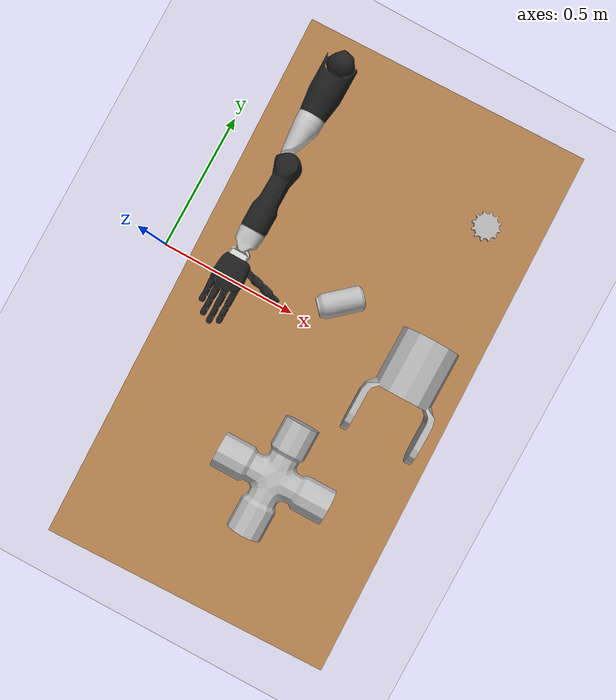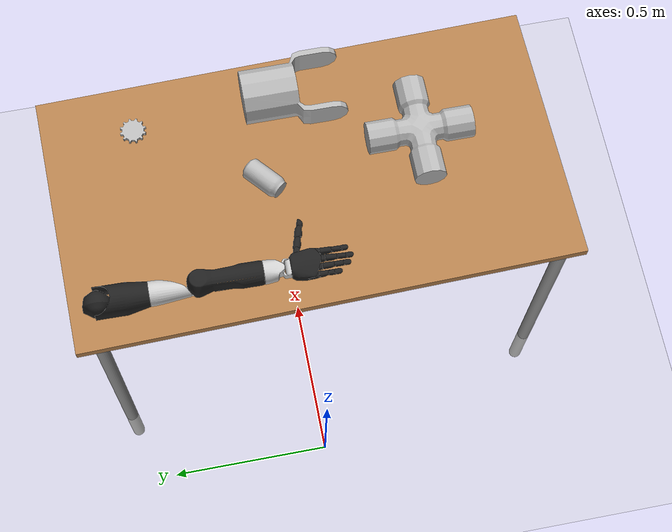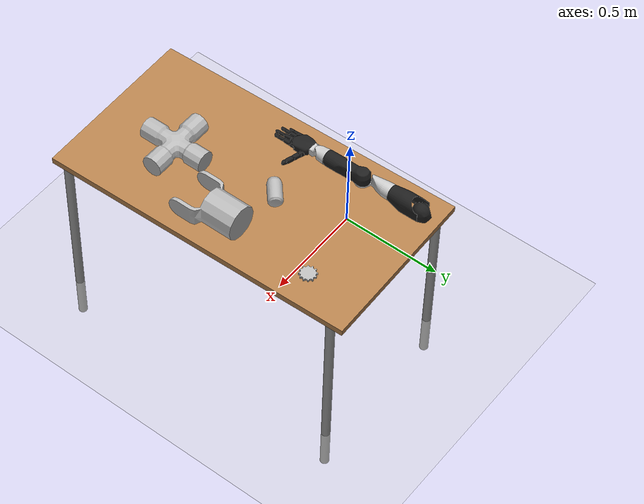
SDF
<sdf version="1.7">
 <world name="default">
  <light name="sun" type="directional">
   <pose>0 0 10 0 -0 0</pose>
   <diffuse>0.8 0.8 0.8 1</diffuse>
   <specular>0.2 0.2 0.2 1</specular>
   <attenuation>
    <range>1000</range>
    <constant>0.9</constant>
    <linear>0.01</linear>
    <quadratic>0.001</quadratic>
   </attenuation>
   <direction>-0.5 0.1 -0.9</direction>
   <spot><inner_angle>0</inner_angle><outer_angle>0</outer_angle><falloff>0</falloff></spot>
  </light>
  <model name="ground_plane">
   <static>1</static>
   <link name="link">
    <collision name="collision">
     <geometry><plane><normal>0 0 1</normal><size>100 100</size></plane></geometry>
     <surface><friction><ode><mu>100</mu><mu2>50</mu2></ode></friction></surface>
    </collision>
    <visual name="visual">
     <cast_shadows>0</cast_shadows>
     <geometry><plane><normal>0 0 1</normal><size>100 100</size></plane></geometry>
     <material>
      <script><uri>file://media/materials/scripts/gazebo.material</uri><name>Gazebo/Grey</name></script>
     </material>
    </visual>
   </link>
  </model>
  <gravity>0 0 -9.8</gravity>
  <magnetic_field>6e-06 2.3e-05 -4.2e-05</magnetic_field>
  <atmosphere type="adiabatic"/>
  <physics type="ode">
   <max_step_size>0.001</max_step_size>
   <real_time_factor>1</real_time_factor>
   <real_time_update_rate>1000</real_time_update_rate>
  </physics>
  <scene><ambient>0.8 0.8 0.8 1</ambient><background>0.7 0.7 0.7 1</background><shadows>1</shadows></scene>
  <audio><device>default</device></audio>
  <spherical_coordinates>
   <surface_model>EARTH_WGS84</surface_model>
   <latitude_deg>0</latitude_deg>
   <longitude_deg>0</longitude_deg>
   <elevation>0</elevation>
   <heading_deg>0</heading_deg>
  </spherical_coordinates>
  <model name="table">
   <static>1</static>
   <link name="link">
    <collision name="surface">
     <pose>0 0 1 0 -0 0</pose>
     <geometry><box><size>1.5 0.8 0.03</size></box></geometry>
     <surface><friction><ode><mu>0.6</mu><mu2>0.6</mu2></ode></friction></surface>
    </collision>
    <visual name="visual1">
     <pose>0 0 1 0 -0 0</pose>
     <geometry><box><size>1.5 0.8 0.03</size></box></geometry>
     <material>
      <script><uri>file://media/materials/scripts/gazebo.material</uri><name>Gazebo/Wood</name></script>
     </material>
    </visual>
    <collision name="front_left_leg">
     <pose>0.68 0.38 0.5 0 -0 0</pose>
     <geometry><cylinder><radius>0.02</radius><length>1</length></cylinder></geometry>
    </collision>
    <visual name="front_left_leg">
     <pose>0.68 0.38 0.5 0 -0 0</pose>
     <geometry><cylinder><radius>0.02</radius><length>1</length></cylinder></geometry>
     <material>
      <script><uri>file://media/materials/scripts/gazebo.material</uri><name>Gazebo/Grey</name></script>
     </material>
    </visual>
    <collision name="front_right_leg">
     <pose>0.68 -0.38 0.5 0 -0 0</pose>
     <geometry><cylinder><radius>0.02</radius><length>1</length></cylinder></geometry>
    </collision>
    <visual name="front_right_leg">
     <pose>0.68 -0.38 0.5 0 -0 0</pose>
     <geometry><cylinder><radius>0.02</radius><length>1</length></cylinder></geometry>
     <material>
      <script><uri>file://media/materials/scripts/gazebo.material</uri><name>Gazebo/Grey</name></script>
     </material>
    </visual>
    <collision name="back_right_leg">
     <pose>-0.68 -0.38 0.5 0 -0 0</pose>
     <geometry><cylinder><radius>0.02</radius><length>1</length></cylinder></geometry>
    </collision>
    <visual name="back_right_leg">
     <pose>-0.68 -0.38 0.5 0 -0 0</pose>
     <geometry><cylinder><radius>0.02</radius><length>1</length></cylinder></geometry>
     <material>
      <script><uri>file://media/materials/scripts/gazebo.material</uri><name>Gazebo/Grey</name></script>
     </material>
    </visual>
    <collision name="back_left_leg">
     <pose>-0.68 0.38 0.5 0 -0 0</pose>
     <geometry><cylinder><radius>0.02</radius><length>1</length></cylinder></geometry>
    </collision>
    <visual name="back_left_leg">
     <pose>-0.68 0.38 0.5 0 -0 0</pose>
     <geometry><cylinder><radius>0.02</radius><length>1</length></cylinder></geometry>
     <material>
      <script><uri>file://media/materials/scripts/gazebo.material</uri><name>Gazebo/Grey</name></script>
     </material>
    </visual>
   </link>
   <pose>0.628743 -0.054706 -0.216115 0 0 -1.54736</pose>
  </model>
  <plugin name="gazebo_link_attacher" filename="libgazebo_link_attacher.so"/>
  <plugin name="gazebo_ros_init" filename="libgazebo_ros_init.so"/>
  <plugin name="gazebo_ros_factory" filename="libgazebo_ros_factory.so"/>
  <model name="coke_can">
   <link name="link">
    <inertial>
     <pose>0 0 0.06 0 -0 0</pose>
     <mass>0.39</mass>
     <inertia>
      <ixx>0.00055575</ixx>
      <ixy>0</ixy>
      <ixz>0</ixz>
      <iyy>0.00055575</iyy>
      <iyz>0</iyz>
      <izz>0.0001755</izz>
     </inertia>
    </inertial>
    <collision name="collision">
     <pose>0.003937 0.004724 -0.18 0 -0 0</pose>
     <geometry><mesh><uri>model://coke_can/meshes/coke_can.dae</uri></mesh></geometry>
     <surface>
      <friction><ode><mu>1</mu><mu2>1</mu2></ode></friction>
      <contact><ode><kp>1e+07</kp><kd>1</kd><min_depth>0.001</min_depth><max_vel>0.1</max_vel></ode></contact>
     </surface>
    </collision>
    <visual name="visual">
     <pose>0.003937 0.004724 -0.18 0 -0 0</pose>
     <geometry><mesh><uri>model://coke_can/meshes/coke_can.dae</uri></mesh></geometry>
    </visual>
   </link>
   <pose>0.680915 0.112378 0.830991 -1.56706 0.784147 2.29425</pose>
  </model>
  <model name="cross_joint_part">
   <link name="link">
    <inertial>
     <pose>0 0 0.048275 0 -0 0</pose>
     <mass>0.5</mass>
     <inertia>
      <ixx>0.00455435</ixx>
      <ixy>0</ixy>
      <ixz>0</ixz>
      <iyy>0.00455435</iyy>
      <iyz>0</iyz>
      <izz>0.00833187</izz>
     </inertia>
    </inertial>
    <collision name="collisionY">
     <pose>0 0 0.048275 1.5707 -0 0</pose>
     <geometry><cylinder><length>0.3162</length><radius>0.0483</radius></cylinder></geometry>
    </collision>
    <collision name="collisionX">
     <pose>0 0 0.048275 0 1.5707 0</pose>
     <geometry><cylinder><length>0.3162</length><radius>0.0483</radius></cylinder></geometry>
    </collision>
    <visual name="visual">
     <geometry><mesh><uri>model://cross_joint_part/meshes/cross_joint.dae</uri></mesh></geometry>
     <material>
      <script>
       <uri>model://arm_part/materials/scripts</uri>
       <uri>model://arm_part/materials/textures</uri>
       <name>ArmPart/Diffuse</name>
      </script>
     </material>
    </visual>
   </link>
   <pose>0.695252 -0.407846 0.798902 0.000111 8.2e-05 0</pose>
  </model>
  <model name="gear_part">
   <link name="link">
    <inertial>
     <pose>0 0 0.005875 0 -0 0</pose>
     <mass>0.5</mass>
     <inertia>
      <ixx>0.000198203</ixx>
      <ixy>0</ixy>
      <ixz>0</ixz>
      <iyy>0.000198203</iyy>
      <iyz>0</iyz>
      <izz>0.000384405</izz>
     </inertia>
    </inertial>
    <collision name="collision">
     <pose>0 0 0.005875 0 -0 0</pose>
     <geometry><cylinder><length>0.012</length><radius>0.0392125</radius></cylinder></geometry>
     <surface><contact><ode><max_vel>0.1</max_vel><min_depth>0.001</min_depth></ode></contact></surface>
    </collision>
    <visual name="visual">
     <geometry><mesh><uri>model://gear_part/meshes/gear.dae</uri><scale>0.25 0.25 0.25</scale></mesh></geometry>
     <material>
      <script>
       <uri>model://arm_part/materials/scripts</uri>
       <uri>model://arm_part/materials/textures</uri>
       <name>ArmPart/Diffuse</name>
      </script>
     </material>
    </visual>
   </link>
   <pose>0.869462 0.426618 0.798572 0 -0 0</pose>
  </model>
  <model name="mpl_right_arm">
   <link name="shoulder">
    <pose>0 0 0.093285 0 0 -0.011537</pose>
    <inertial>
     <pose>0.000536 0.002002 0.03328 0 -0 0</pose>
     <mass>0.0363799</mass>
     <inertia>
      <ixx>3.73005e-05</ixx>
      <ixy>5.68571e-07</ixy>
      <ixz>-7.59543e-07</ixz>
      <iyy>2.60558e-05</iyy>
      <iyz>-9.15512e-07</iyz>
      <izz>3.86186e-05</izz>
     </inertia>
    </inertial>
    <collision name="collision">
     <pose>0 0 0.0345 0 -0 0</pose>
     <geometry><sphere><radius>0.03495</radius></sphere></geometry>
     <surface>
      <contact><ode><kp>100000</kp><kd>10</kd><max_vel>0.1</max_vel><min_depth>0.0015</min_depth></ode></contact>
     </surface>
    </collision>
    <collision name="collision_1">
     <pose>0 0 0.01892 0 -0 0</pose>
     <geometry><cylinder><radius>0.038</radius><length>0.03784</length></cylinder></geometry>
     <surface>
      <contact><ode><kp>100000</kp><kd>10</kd><max_vel>0.1</max_vel><min_depth>0.0015</min_depth></ode></contact>
     </surface>
    </collision>
    <visual name="visual">
     <geometry><mesh><uri>model://mpl_right_arm/meshes/shoulder.stl</uri></mesh></geometry>
     <material><script><name>Gazebo/FlatBlack</name><uri>__default__</uri></script></material>
    </visual>
   </link>
   <link name="humerus">
    <pose>0.001643 -1.9e-05 0.12058 0 0 -0.011537</pose>
    <inertial>
     <pose>-0.00523 -0.083481 0.010842 0 -0 0</pose>
     <mass>0.0857896</mass>
     <inertia>
      <ixx>0.000259543</ixx>
      <ixy>-4.20463e-06</ixy>
      <ixz>9.18286e-07</ixz>
      <iyy>0.000134353</iyy>
      <iyz>-1.37928e-05</iyz>
      <izz>0.000284981</izz>
     </inertia>
    </inertial>
    <collision name="collision">
     <pose>-0.00164 -0.07024 0.01366 1.5707 -0 0</pose>
     <geometry><cylinder><radius>0.037035</radius><length>0.15849</length></cylinder></geometry>
     <surface>
      <contact><ode><kp>100000</kp><kd>10</kd><max_vel>0.1</max_vel><min_depth>0.0015</min_depth></ode></contact>
     </surface>
    </collision>
    <visual name="visual">
     <geometry><mesh><uri>model://mpl_right_arm/meshes/humerus.stl</uri></mesh></geometry>
     <material><script><name>Gazebo/FlatBlack</name><uri>__default__</uri></script></material>
    </visual>
   </link>
   <link name="elbow">
    <pose>-0.001728 -0.150057 0.134471 0 0 -0.011537</pose>
    <inertial>
     <pose>0.001164 -0.074089 -0.007315 0 -0 0</pose>
     <mass>0.0351897</mass>
     <inertia>
      <ixx>0.000106583</ixx>
      <ixy>-5.90862e-06</ixy>
      <ixz>-2.34382e-06</ixz>
      <iyy>3.29639e-05</iyy>
      <iyz>1.56515e-05</iyz>
      <izz>0.000106705</izz>
     </inertia>
    </inertial>
    <collision name="collision">
     <pose>0 -0.05957 0.00147 1.5707 -0 0</pose>
     <geometry><cylinder><radius>0.03447</radius><length>0.11914</length></cylinder></geometry>
     <surface>
      <contact><ode><kp>100000</kp><kd>10</kd><max_vel>0.1</max_vel><min_depth>0.0015</min_depth></ode></contact>
     </surface>
    </collision>
    <collision name="collision_1">
     <pose>0.00997 -0.1445 -0.0245 0 -0 0</pose>
     <geometry><cylinder><radius>0.036</radius><length>0.018</length></cylinder></geometry>
     <surface>
      <contact><ode><kp>100000</kp><kd>10</kd><max_vel>0.1</max_vel><min_depth>0.0015</min_depth></ode></contact>
     </surface>
    </collision>
    <visual name="visual">
     <geometry><mesh><uri>model://mpl_right_arm/meshes/elbow.stl</uri></mesh></geometry>
     <material>
      <ambient>0.2 0.2 0.2 1</ambient>
      <diffuse>0.8 0.8 0.8 1</diffuse>
      <specular>0.9 0.9 0.9 1</specular>
     </material>
    </visual>
   </link>
   <link name="forearm">
    <pose>0.006605 -0.294573 0.119123 0 0 -0.011537</pose>
    <inertial>
     <pose>-0.000589 -0.073314 0.021553 0 -0 0</pose>
     <mass>0.0997005</mass>
     <inertia>
      <ixx>0.0004998</ixx>
      <ixy>-5.83136e-06</ixy>
      <ixz>3.56083e-07</ixz>
      <iyy>0.00010215</iyy>
      <iyz>3.76069e-05</iyz>
      <izz>0.000498862</izz>
     </inertia>
    </inertial>
    <collision name="collision">
     <pose>0 0 0.02855 0 -0 0</pose>
     <geometry><cylinder><radius>0.03567</radius><length>0.0571</length></cylinder></geometry>
     <surface>
      <contact><ode><kp>100000</kp><kd>10</kd><max_vel>0.1</max_vel><min_depth>0.0015</min_depth></ode></contact>
     </surface>
    </collision>
    <collision name="collision_1">
     <pose>0 -0.10745 0.016 1.5707 -0 0</pose>
     <geometry><cylinder><radius>0.035</radius><length>0.148</length></cylinder></geometry>
     <surface>
      <contact><ode><kp>100000</kp><kd>10</kd><max_vel>0.1</max_vel><min_depth>0.0015</min_depth></ode></contact>
     </surface>
    </collision>
    <visual name="visual">
     <geometry><mesh><uri>model://mpl_right_arm/meshes/forearm.stl</uri></mesh></geometry>
     <material><script><name>Gazebo/FlatBlack</name><uri>__default__</uri></script></material>
    </visual>
    <sensor name="forearm_contact_sensor" type="contact">
     <contact>
      <collision>collision</collision>
      <collision>collision_1</collision>
      <topic>~/forearm/contact</topic>
     </contact>
    </sensor>
   </link>
   <link name="wristy">
    <pose>0.004499 -0.479995 0.135123 0 0 -0.011537</pose>
    <inertial>
     <pose>-7.1e-05 -0.021779 -0.000286 0 -0 0</pose>
     <mass>0.0272932</mass>
     <inertia>
      <ixx>1.77029e-05</ixx>
      <ixy>7.89061e-09</ixy>
      <ixz>4.33867e-09</ixz>
      <iyy>2.46772e-05</iyy>
      <iyz>1.77331e-07</iyz>
      <izz>1.7112e-05</izz>
     </inertia>
    </inertial>
    <collision name="collision">
     <pose>0 -0.025 0 1.5707 -0 0</pose>
     <geometry><cylinder><radius>0.03447</radius><length>0.05</length></cylinder></geometry>
     <surface>
      <contact><ode><kp>100000</kp><kd>10</kd><max_vel>0.1</max_vel><min_depth>0.0015</min_depth></ode></contact>
     </surface>
    </collision>
    <visual name="visual">
     <geometry><mesh><uri>model://mpl_right_arm/meshes/wristy.stl</uri></mesh></geometry>
     <material>
      <ambient>0.2 0.2 0.2 1</ambient>
      <diffuse>0.8 0.8 0.8 1</diffuse>
      <specular>0.9 0.9 0.9 1</specular>
     </material>
    </visual>
    <sensor name="wristy_contact_sensor" type="contact">
     <contact><collision>collision</collision><topic>~/wristy/contact</topic></contact>
    </sensor>
   </link>
   <link name="wristx">
    <pose>0.003916 -0.527636 0.137161 0 0 -0.011537</pose>
    <inertial>
     <pose>0.001392 -0.009752 -0.002527 0 -0 0</pose>
     <mass>0.010691</mass>
     <inertia>
      <ixx>3.27995e-06</ixx>
      <ixy>-1.50151e-07</ixy>
      <ixz>5.11904e-09</ixz>
      <iyy>4.22942e-06</iyy>
      <iyz>-4.20007e-08</iyz>
      <izz>5.04229e-06</izz>
     </inertia>
    </inertial>
    <collision name="collision">
     <pose>0 0 -0.00314 0 -0 0</pose>
     <geometry><cylinder><radius>0.01473</radius><length>0.04478</length></cylinder></geometry>
     <surface>
      <contact><ode><kp>100000</kp><kd>10</kd><max_vel>0.1</max_vel><min_depth>0.0015</min_depth></ode></contact>
     </surface>
    </collision>
    <collision name="collision_1">
     <pose>0.0236 -0.02969 -0.0024 0 1.5707 0</pose>
     <geometry><cylinder><radius>0.013175</radius><length>0.005</length></cylinder></geometry>
     <surface>
      <contact><ode><kp>100000</kp><kd>10</kd><max_vel>0.1</max_vel><min_depth>0.0015</min_depth></ode></contact>
     </surface>
    </collision>
    <collision name="collision_2">
     <pose>-0.0236 -0.02969 -0.0024 0 1.5707 0</pose>
     <geometry><cylinder><radius>0.013175</radius><length>0.005</length></cylinder></geometry>
     <surface>
      <contact><ode><kp>100000</kp><kd>10</kd><max_vel>0.1</max_vel><min_depth>0.0015</min_depth></ode></contact>
     </surface>
    </collision>
    <visual name="visual">
     <geometry><mesh><uri>model://mpl_right_arm/meshes/wristx.stl</uri></mesh></geometry>
     <material>
      <ambient>0.2 0.2 0.2 1</ambient>
      <diffuse>0.8 0.8 0.8 1</diffuse>
      <specular>0.9 0.9 0.9 1</specular>
     </material>
    </visual>
    <sensor name="wristx_contact_sensor" type="contact">
     <contact>
      <collision>collision</collision>
      <collision>collision_1</collision>
      <collision>collision_2</collision>
      <topic>~/wristx/contact</topic>
     </contact>
    </sensor>
   </link>
   <link name="wristz">
    <pose>0.003757 -0.557636 0.135067 0 0 -0.011537</pose>
    <inertial>
     <pose>0.003682 -0.035876 0.002659 0 -0 0</pose>
     <mass>0.125889</mass>
     <inertia>
      <ixx>8.18077e-05</ixx>
      <ixy>-9.44149e-06</ixy>
      <ixz>3.88366e-06</ixz>
      <iyy>9.81482e-05</iyy>
      <iyz>-4.84151e-08</iyz>
      <izz>0.000131783</izz>
     </inertia>
    </inertial>
    <collision name="collision">
     <pose>0.00207 -0.00047 0.00046 1.5707 0 1.5707</pose>
     <geometry><cylinder><radius>0.01411</radius><length>0.04482</length></cylinder></geometry>
     <surface>
      <contact><ode><kp>100000</kp><kd>10</kd><max_vel>0.1</max_vel><min_depth>0.0015</min_depth></ode></contact>
     </surface>
    </collision>
    <collision name="collision_palm">
     <pose>0.002 -0.03739 0 0 -0 0</pose>
     <geometry><box><size>0.07928 0.08316 0.04402</size></box></geometry>
     <surface>
      <contact><ode><kp>100000</kp><kd>100</kd><max_vel>0.1</max_vel><min_depth>0.0015</min_depth></ode></contact>
     </surface>
    </collision>
    <visual name="visual">
     <geometry><mesh><uri>model://mpl_right_arm/meshes/wristz.stl</uri></mesh></geometry>
     <material>
      <ambient>0.2 0.2 0.2 1</ambient>
      <diffuse>0.8 0.8 0.8 1</diffuse>
      <specular>0.9 0.9 0.9 1</specular>
     </material>
    </visual>
    <visual name="visual_palm">
     <pose>0.025625 0 0 0 -0 0</pose>
     <geometry><mesh><uri>model://mpl_right_arm/meshes/palm.stl</uri></mesh></geometry>
     <material><script><name>Gazebo/FlatBlack</name><uri>__default__</uri></script></material>
    </visual>
    <sensor name="palm_contact_sensor" type="contact">
     <contact><collision>collision_palm</collision><topic>~/palm/contact</topic></contact>
    </sensor>
   </link>
   <link name="index0">
    <pose>0.038485 -0.623842 0.136079 0 0.174533 -0.011537</pose>
    <inertial>
     <pose>-0.000143 -0.005485 0.000206 0 -0 0</pose>
     <mass>0.00295579</mass>
     <inertia>
      <ixx>4.22375e-07</ixx>
      <ixy>4.23313e-09</ixy>
      <ixz>5.00708e-10</ixz>
      <iyy>1.94048e-07</iyy>
      <iyz>-4.58697e-09</iyz>
      <izz>4.02188e-07</izz>
     </inertia>
    </inertial>
    <collision name="collision">
     <pose>0 -0.01339 0 1.5707 -0 0</pose>
     <geometry><cylinder><length>0.028</length><radius>0.01</radius></cylinder></geometry>
     <surface>
      <contact><ode><kp>100000</kp><kd>10</kd><max_vel>0.1</max_vel><min_depth>0.0015</min_depth></ode></contact>
     </surface>
    </collision>
    <visual name="visual">
     <geometry><mesh><uri>model://mpl_right_arm/meshes/index0.stl</uri></mesh></geometry>
     <material><script><name>Gazebo/FlatBlack</name><uri>__default__</uri></script></material>
    </visual>
    <sensor name="index0_contact_sensor" type="contact">
     <contact><collision>collision</collision><topic>~/index0/contact</topic></contact>
    </sensor>
   </link>
   <link name="index1">
    <pose>0.038339 -0.641841 0.136068 0 0.174533 -0.011537</pose>
    <inertial>
     <pose>0.000406 -0.021313 0.000656 0 -0 0</pose>
     <mass>0.00478235</mass>
     <inertia>
      <ixx>8.18593e-07</ixx>
      <ixy>-1.2874e-09</ixy>
      <ixz>1.78664e-10</ixz>
      <iyy>3.06547e-07</iyy>
      <iyz>-1.18998e-08</iyz>
      <izz>7.95406e-07</izz>
     </inertia>
    </inertial>
    <collision name="collision">
     <pose>0 -0.02782 0 1.5707 -0 0</pose>
     <geometry><cylinder><radius>0.01</radius><length>0.02781</length></cylinder></geometry>
     <surface>
      <contact><ode><kp>100000</kp><kd>10</kd><max_vel>0.1</max_vel><min_depth>0.0015</min_depth></ode></contact>
     </surface>
    </collision>
    <visual name="visual">
     <geometry><mesh><uri>model://mpl_right_arm/meshes/index1.stl</uri></mesh></geometry>
     <material><script><name>Gazebo/FlatBlack</name><uri>__default__</uri></script></material>
    </visual>
    <sensor name="index1_contact_sensor" type="contact">
     <contact><collision>collision</collision><topic>~/index1/contact</topic></contact>
    </sensor>
   </link>
   <link name="index2">
    <pose>0.038994 -0.685352 0.136372 0 0.174533 -0.011537</pose>
    <inertial>
     <pose>-0.000841 -0.012689 0.000573 0 -0 0</pose>
     <mass>0.00344764</mass>
     <inertia>
      <ixx>3.63785e-07</ixx>
      <ixy>-6.41791e-09</ixy>
      <ixz>7.97765e-10</ixz>
      <iyy>1.07105e-07</iyy>
      <iyz>2.03273e-08</iyz>
      <izz>3.57435e-07</izz>
     </inertia>
    </inertial>
    <collision name="collision">
     <pose>0 -0.01152 0 1.5707 -0 0</pose>
     <geometry><cylinder><length>0.029</length><radius>0.0075</radius></cylinder></geometry>
     <surface>
      <contact><ode><kp>100000</kp><kd>10</kd><max_vel>0.1</max_vel><min_depth>0.0015</min_depth></ode></contact>
     </surface>
    </collision>
    <collision name="collision_1">
     <pose>0 -0.02502 0 0 -0 0</pose>
     <geometry><sphere><radius>0.0075</radius></sphere></geometry>
     <surface>
      <contact><ode><kp>100000</kp><kd>10</kd><max_vel>0.1</max_vel><min_depth>0.0015</min_depth></ode></contact>
     </surface>
    </collision>
    <visual name="visual">
     <geometry><mesh><uri>model://mpl_right_arm/meshes/index2.stl</uri></mesh></geometry>
     <material><script><name>Gazebo/FlatBlack</name><uri>__default__</uri></script></material>
    </visual>
    <sensor name="index2_contact_sensor" type="contact">
     <contact>
      <collision>collision</collision>
      <collision>collision_1</collision>
      <topic>~/index2/contact</topic>
     </contact>
    </sensor>
   </link>
   <link name="index3">
    <pose>0.038086 -0.709843 0.136482 0 0.174533 -0.011537</pose>
    <inertial>
     <pose>4.3e-05 -0.012532 0.000903 0 -0 0</pose>
     <mass>0.00274415</mass>
     <inertia>
      <ixx>1.09202e-07</ixx>
      <ixy>-3.99165e-12</ixy>
      <ixz>-5.84792e-12</ixz>
      <iyy>7.79728e-08</iyy>
      <iyz>2.77966e-09</iyz>
      <izz>1.19449e-07</izz>
     </inertia>
    </inertial>
    <collision name="collision">
     <pose>0 -0.00688 0.0001 1.5707 -0 0</pose>
     <geometry><cylinder><length>0.01376</length><radius>0.0074</radius></cylinder></geometry>
     <surface>
      <contact><ode><kp>100000</kp><kd>10</kd><max_vel>0.1</max_vel><min_depth>0.0015</min_depth></ode></contact>
     </surface>
    </collision>
    <collision name="collision_1">
     <pose>0 -0.015 0.0001 0 -0 0</pose>
     <geometry><sphere><radius>0.0072</radius></sphere></geometry>
     <surface>
      <contact><ode><kp>100000</kp><kd>10</kd><max_vel>0.1</max_vel><min_depth>0.0015</min_depth></ode></contact>
     </surface>
    </collision>
    <visual name="visual">
     <geometry><mesh><uri>model://mpl_right_arm/meshes/index3.stl</uri></mesh></geometry>
     <material><script><name>Gazebo/FlatBlack</name><uri>__default__</uri></script></material>
    </visual>
    <sensor name="index3_contact_sensor" type="contact">
     <contact>
      <collision>collision</collision>
      <collision>collision_1</collision>
      <topic>~/index3/contact</topic>
     </contact>
    </sensor>
    <sensor name="index3_imu_sensor" type="imu">
     <always_on>1</always_on>
     <update_rate>1000</update_rate>
     <imu>
      <angular_velocity>
       <x>
        <noise type="gaussian">
         <mean>0</mean>
         <stddev>0.0002</stddev>
         <bias_mean>7.5e-06</bias_mean>
         <bias_stddev>8e-07</bias_stddev>
        </noise>
       </x>
       <y>
        <noise type="gaussian">
         <mean>0</mean>
         <stddev>0.0002</stddev>
         <bias_mean>7.5e-06</bias_mean>
         <bias_stddev>8e-07</bias_stddev>
        </noise>
       </y>
       <z>
        <noise type="gaussian">
         <mean>0</mean>
         <stddev>0.0002</stddev>
         <bias_mean>7.5e-06</bias_mean>
         <bias_stddev>8e-07</bias_stddev>
        </noise>
       </z>
      </angular_velocity>
      <linear_acceleration>
       <x>
        <noise type="gaussian">
         <mean>0</mean>
         <stddev>0.017</stddev>
         <bias_mean>0.1</bias_mean>
         <bias_stddev>0.001</bias_stddev>
        </noise>
       </x>
       <y>
        <noise type="gaussian">
         <mean>0</mean>
         <stddev>0.017</stddev>
         <bias_mean>0.1</bias_mean>
         <bias_stddev>0.001</bias_stddev>
        </noise>
       </y>
       <z>
        <noise type="gaussian">
         <mean>0</mean>
         <stddev>0.017</stddev>
         <bias_mean>0.1</bias_mean>
         <bias_stddev>0.001</bias_stddev>
        </noise>
       </z>
      </linear_acceleration>
     </imu>
    </sensor>
   </link>
   <link name="middle0">
    <pose>0.015668 -0.63568 0.140513 0.087267 0 -0.011537</pose>
    <inertial>
     <pose>-0.000143 -0.005485 0.000206 0 -0 0</pose>
     <mass>0.00295579</mass>
     <inertia>
      <ixx>4.22374e-07</ixx>
      <ixy>4.23312e-09</ixy>
      <ixz>5.00706e-10</ixz>
      <iyy>1.94048e-07</iyy>
      <iyz>-4.58725e-09</iyz>
      <izz>4.02189e-07</izz>
     </inertia>
    </inertial>
    <collision name="collision">
     <pose>0 -0.01339 0 1.5707 -0 0</pose>
     <geometry><cylinder><length>0.028</length><radius>0.01</radius></cylinder></geometry>
     <surface>
      <contact><ode><kp>100000</kp><kd>10</kd><max_vel>0.1</max_vel><min_depth>0.0015</min_depth></ode></contact>
     </surface>
    </collision>
    <visual name="visual">
     <geometry><mesh><uri>model://mpl_right_arm/meshes/middle0.stl</uri></mesh></geometry>
     <material><script><name>Gazebo/FlatBlack</name><uri>__default__</uri></script></material>
    </visual>
    <sensor name="middle0_contact_sensor" type="contact">
     <contact><collision>collision</collision><topic>~/middle0/contact</topic></contact>
    </sensor>
   </link>
   <link name="middle1">
    <pose>0.015524 -0.653612 0.138944 0.087266 -0 -0.011537</pose>
    <inertial>
     <pose>0.000406 -0.021313 0.000656 0 -0 0</pose>
     <mass>0.00478229</mass>
     <inertia>
      <ixx>8.1859e-07</ixx>
      <ixy>-1.28827e-09</ixy>
      <ixz>1.7867e-10</ixz>
      <iyy>3.06545e-07</iyy>
      <iyz>-1.19001e-08</iyz>
      <izz>7.95403e-07</izz>
     </inertia>
    </inertial>
    <collision name="collision">
     <pose>0 -0.025 0 1.5707 -0 0</pose>
     <geometry><cylinder><radius>0.01</radius><length>0.03459</length></cylinder></geometry>
     <surface>
      <contact><ode><kp>100000</kp><kd>10</kd><max_vel>0.1</max_vel><min_depth>0.0015</min_depth></ode></contact>
     </surface>
    </collision>
    <visual name="visual">
     <geometry><mesh><uri>model://mpl_right_arm/meshes/middle1.stl</uri></mesh></geometry>
     <material><script><name>Gazebo/FlatBlack</name><uri>__default__</uri></script></material>
    </visual>
    <sensor name="middle1_contact_sensor" type="contact">
     <contact><collision>collision</collision><topic>~/middle1/contact</topic></contact>
    </sensor>
   </link>
   <link name="middle2">
    <pose>0.01611 -0.696999 0.135651 0.087267 0 -0.011537</pose>
    <inertial>
     <pose>-0.000841 -0.012689 0.000573 0 -0 0</pose>
     <mass>0.00344765</mass>
     <inertia>
      <ixx>3.63785e-07</ixx>
      <ixy>-6.41794e-09</ixy>
      <ixz>7.97197e-10</ixz>
      <iyy>1.07106e-07</iyy>
      <iyz>2.03275e-08</iyz>
      <izz>3.57435e-07</izz>
     </inertia>
    </inertial>
    <collision name="collision">
     <pose>0 -0.01152 0 1.5707 -0 0</pose>
     <geometry><cylinder><length>0.029</length><radius>0.0075</radius></cylinder></geometry>
     <surface>
      <contact><ode><kp>100000</kp><kd>10</kd><max_vel>0.1</max_vel><min_depth>0.0015</min_depth></ode></contact>
     </surface>
    </collision>
    <collision name="collision_1">
     <pose>0 -0.02302 0 0 -0 0</pose>
     <geometry><sphere><radius>0.0075</radius></sphere></geometry>
     <surface>
      <contact><ode><kp>100000</kp><kd>10</kd><max_vel>0.1</max_vel><min_depth>0.0015</min_depth></ode></contact>
     </surface>
    </collision>
    <visual name="visual">
     <geometry><mesh><uri>model://mpl_right_arm/meshes/middle2.stl</uri></mesh></geometry>
     <material><script><name>Gazebo/FlatBlack</name><uri>__default__</uri></script></material>
    </visual>
    <sensor name="middle2_contact_sensor" type="contact">
     <contact>
      <collision>collision</collision>
      <collision>collision_1</collision>
      <topic>~/middle2/contact</topic>
     </contact>
    </sensor>
   </link>
   <link name="middle3">
    <pose>0.015193 -0.721397 0.133515 0.087266 -0 -0.011537</pose>
    <inertial>
     <pose>4.3e-05 -0.012532 0.000903 0 -0 0</pose>
     <mass>0.00274417</mass>
     <inertia>
      <ixx>1.09202e-07</ixx>
      <ixy>-3.78001e-12</ixy>
      <ixz>-5.35395e-12</ixz>
      <iyy>7.79738e-08</iyy>
      <iyz>2.77969e-09</iyz>
      <izz>1.1945e-07</izz>
     </inertia>
    </inertial>
    <collision name="collision">
     <pose>0 -0.00688 0.0001 1.5707 -0 0</pose>
     <geometry><cylinder><length>0.01376</length><radius>0.0074</radius></cylinder></geometry>
     <surface>
      <contact><ode><kp>100000</kp><kd>10</kd><max_vel>0.1</max_vel><min_depth>0.0015</min_depth></ode></contact>
     </surface>
    </collision>
    <collision name="collision_1">
     <pose>0 -0.015 0.0001 0 -0 0</pose>
     <geometry><sphere><radius>0.0072</radius></sphere></geometry>
     <surface>
      <contact><ode><kp>100000</kp><kd>10</kd><max_vel>0.1</max_vel><min_depth>0.0015</min_depth></ode></contact>
     </surface>
    </collision>
    <visual name="visual">
     <geometry><mesh><uri>model://mpl_right_arm/meshes/middle3.stl</uri></mesh></geometry>
     <material><script><name>Gazebo/FlatBlack</name><uri>__default__</uri></script></material>
    </visual>
    <sensor name="middle3_contact_sensor" type="contact">
     <contact>
      <collision>collision</collision>
      <collision>collision_1</collision>
      <topic>~/middle3/contact</topic>
     </contact>
    </sensor>
    <sensor name="middle3_imu_sensor" type="imu">
     <always_on>1</always_on>
     <update_rate>1000</update_rate>
     <imu>
      <angular_velocity>
       <x>
        <noise type="gaussian">
         <mean>0</mean>
         <stddev>0.0002</stddev>
         <bias_mean>7.5e-06</bias_mean>
         <bias_stddev>8e-07</bias_stddev>
        </noise>
       </x>
       <y>
        <noise type="gaussian">
         <mean>0</mean>
         <stddev>0.0002</stddev>
         <bias_mean>7.5e-06</bias_mean>
         <bias_stddev>8e-07</bias_stddev>
        </noise>
       </y>
       <z>
        <noise type="gaussian">
         <mean>0</mean>
         <stddev>0.0002</stddev>
         <bias_mean>7.5e-06</bias_mean>
         <bias_stddev>8e-07</bias_stddev>
        </noise>
       </z>
      </angular_velocity>
      <linear_acceleration>
       <x>
        <noise type="gaussian">
         <mean>0</mean>
         <stddev>0.017</stddev>
         <bias_mean>0.1</bias_mean>
         <bias_stddev>0.001</bias_stddev>
        </noise>
       </x>
       <y>
        <noise type="gaussian">
         <mean>0</mean>
         <stddev>0.017</stddev>
         <bias_mean>0.1</bias_mean>
         <bias_stddev>0.001</bias_stddev>
        </noise>
       </y>
       <z>
        <noise type="gaussian">
         <mean>0</mean>
         <stddev>0.017</stddev>
         <bias_mean>0.1</bias_mean>
         <bias_stddev>0.001</bias_stddev>
        </noise>
       </z>
      </linear_acceleration>
     </imu>
    </sensor>
   </link>
   <link name="pinky0">
    <pose>-0.027501 -0.61268 0.129428 0 -0.174533 -0.011537</pose>
    <inertial>
     <pose>-0.000143 -0.005385 0.000206 0 -0 0</pose>
     <mass>0.00295579</mass>
     <inertia>
      <ixx>4.22375e-07</ixx>
      <ixy>4.23309e-09</ixy>
      <ixz>5.0054e-10</ixz>
      <iyy>1.94048e-07</iyy>
      <iyz>-4.58693e-09</iyz>
      <izz>4.02189e-07</izz>
     </inertia>
    </inertial>
    <collision name="collision">
     <pose>0 -0.01339 0 1.5707 -0 0</pose>
     <geometry><cylinder><length>0.028</length><radius>0.01</radius></cylinder></geometry>
     <surface>
      <contact><ode><kp>100000</kp><kd>10</kd><max_vel>0.1</max_vel><min_depth>0.0015</min_depth></ode></contact>
     </surface>
    </collision>
    <visual name="visual">
     <geometry><mesh><uri>model://mpl_right_arm/meshes/pinky0.stl</uri></mesh></geometry>
     <material><script><name>Gazebo/FlatBlack</name><uri>__default__</uri></script></material>
    </visual>
    <sensor name="pinky0_contact_sensor" type="contact">
     <contact><collision>collision</collision><topic>~/pinky0/contact</topic></contact>
    </sensor>
   </link>
   <link name="pinky1">
    <pose>-0.027646 -0.630579 0.129439 0 -0.174533 -0.011537</pose>
    <inertial>
     <pose>0.000459 -0.016048 0.000925 0 -0 0</pose>
     <mass>0.0034099</mass>
     <inertia>
      <ixx>4.03282e-07</ixx>
      <ixy>-1.80186e-09</ixy>
      <ixz>-1.42049e-09</ixz>
      <iyy>2.20449e-07</iyy>
      <iyz>-9.60174e-09</iyz>
      <izz>3.83588e-07</izz>
     </inertia>
    </inertial>
    <collision name="collision">
     <pose>0 -0.02082 0 1.5707 -0 0</pose>
     <geometry><cylinder><radius>0.01</radius><length>0.02381</length></cylinder></geometry>
     <surface>
      <contact><ode><kp>100000</kp><kd>10</kd><max_vel>0.1</max_vel><min_depth>0.0015</min_depth></ode></contact>
     </surface>
    </collision>
    <visual name="visual">
     <geometry><mesh><uri>model://mpl_right_arm/meshes/pinky1.stl</uri></mesh></geometry>
     <material><script><name>Gazebo/FlatBlack</name><uri>__default__</uri></script></material>
    </visual>
    <sensor name="pinky1_contact_sensor" type="contact">
     <contact><collision>collision</collision><topic>~/pinky0/contact</topic></contact>
    </sensor>
   </link>
   <link name="pinky2">
    <pose>-0.027544 -0.663582 0.130032 0 -0.174533 -0.011537</pose>
    <inertial>
     <pose>-0.000271 -0.009146 0.000738 0 -0 0</pose>
     <mass>0.00250622</mass>
     <inertia>
      <ixx>1.78939e-07</ixx>
      <ixy>-3.88097e-09</ixy>
      <ixz>3.24897e-10</ixz>
      <iyy>7.59883e-08</iyy>
      <iyz>1.17825e-08</iyz>
      <izz>1.74551e-07</izz>
     </inertia>
    </inertial>
    <collision name="collision">
     <pose>0 -0.0076 0 1.5707 -0 0</pose>
     <geometry><cylinder><length>0.029</length><radius>0.0075</radius></cylinder></geometry>
     <surface>
      <contact><ode><kp>100000</kp><kd>10</kd><max_vel>0.1</max_vel><min_depth>0.0015</min_depth></ode></contact>
     </surface>
    </collision>
    <visual name="visual">
     <geometry><mesh><uri>model://mpl_right_arm/meshes/pinky2.stl</uri></mesh></geometry>
     <material><script><name>Gazebo/FlatBlack</name><uri>__default__</uri></script></material>
    </visual>
    <sensor name="pinky2_contact_sensor" type="contact">
     <contact><collision>collision</collision><topic>~/pinky2/contact</topic></contact>
    </sensor>
   </link>
   <link name="pinky3">
    <pose>-0.027793 -0.681081 0.130023 0 -0.174533 -0.011537</pose>
    <inertial>
     <pose>3.9e-05 -0.012505 0.000912 0 -0 0</pose>
     <mass>0.00273265</mass>
     <inertia>
      <ixx>1.08629e-07</ixx>
      <ixy>2.84178e-11</ixy>
      <ixz>1.88869e-11</ixz>
      <iyy>7.78965e-08</iyy>
      <iyz>2.64344e-09</iyz>
      <izz>1.18971e-07</izz>
     </inertia>
    </inertial>
    <collision name="collision">
     <pose>0 -0.00688 0.0001 1.5707 -0 0</pose>
     <geometry><cylinder><length>0.01376</length><radius>0.0074</radius></cylinder></geometry>
     <surface>
      <contact><ode><kp>100000</kp><kd>10</kd><max_vel>0.1</max_vel><min_depth>0.0015</min_depth></ode></contact>
     </surface>
    </collision>
    <collision name="collision_1">
     <pose>0 -0.015 0.0001 0 -0 0</pose>
     <geometry><sphere><radius>0.0072</radius></sphere></geometry>
     <surface>
      <contact><ode><kp>100000</kp><kd>10</kd><max_vel>0.1</max_vel><min_depth>0.0015</min_depth></ode></contact>
     </surface>
    </collision>
    <visual name="visual">
     <geometry><mesh><uri>model://mpl_right_arm/meshes/pinky3.stl</uri></mesh></geometry>
     <material><script><name>Gazebo/FlatBlack</name><uri>__default__</uri></script></material>
    </visual>
    <sensor name="pinky3_contact_sensor" type="contact">
     <contact>
      <collision>collision</collision>
      <collision>collision_1</collision>
      <topic>~/pinky3/contact</topic>
     </contact>
    </sensor>
    <sensor name="pinky3_imu_sensor" type="imu">
     <always_on>1</always_on>
     <update_rate>1000</update_rate>
     <imu>
      <angular_velocity>
       <x>
        <noise type="gaussian">
         <mean>0</mean>
         <stddev>0.0002</stddev>
         <bias_mean>7.5e-06</bias_mean>
         <bias_stddev>8e-07</bias_stddev>
        </noise>
       </x>
       <y>
        <noise type="gaussian">
         <mean>0</mean>
         <stddev>0.0002</stddev>
         <bias_mean>7.5e-06</bias_mean>
         <bias_stddev>8e-07</bias_stddev>
        </noise>
       </y>
       <z>
        <noise type="gaussian">
         <mean>0</mean>
         <stddev>0.0002</stddev>
         <bias_mean>7.5e-06</bias_mean>
         <bias_stddev>8e-07</bias_stddev>
        </noise>
       </z>
      </angular_velocity>
      <linear_acceleration>
       <x>
        <noise type="gaussian">
         <mean>0</mean>
         <stddev>0.017</stddev>
         <bias_mean>0.1</bias_mean>
         <bias_stddev>0.001</bias_stddev>
        </noise>
       </x>
       <y>
        <noise type="gaussian">
         <mean>0</mean>
         <stddev>0.017</stddev>
         <bias_mean>0.1</bias_mean>
         <bias_stddev>0.001</bias_stddev>
        </noise>
       </y>
       <z>
        <noise type="gaussian">
         <mean>0</mean>
         <stddev>0.017</stddev>
         <bias_mean>0.1</bias_mean>
         <bias_stddev>0.001</bias_stddev>
        </noise>
       </z>
      </linear_acceleration>
     </imu>
    </sensor>
   </link>
   <link name="ring0">
    <pose>-0.00688 -0.624218 0.136579 0 -0.174533 -0.011537</pose>
    <inertial>
     <pose>-0.000143 -0.005485 0.000206 0 -0 0</pose>
     <mass>0.00295579</mass>
     <inertia>
      <ixx>4.22375e-07</ixx>
      <ixy>4.23309e-09</ixy>
      <ixz>5.00535e-10</ixz>
      <iyy>1.94048e-07</iyy>
      <iyz>-4.58693e-09</iyz>
      <izz>4.02189e-07</izz>
     </inertia>
    </inertial>
    <collision name="collision">
     <pose>0 -0.01339 0 1.5707 -0 0</pose>
     <geometry><cylinder><length>0.028</length><radius>0.01</radius></cylinder></geometry>
     <surface>
      <contact><ode><kp>100000</kp><kd>10</kd><max_vel>0.1</max_vel><min_depth>0.0015</min_depth></ode></contact>
     </surface>
    </collision>
    <visual name="visual">
     <geometry><mesh><uri>model://mpl_right_arm/meshes/ring0.stl</uri></mesh></geometry>
     <material><script><name>Gazebo/FlatBlack</name><uri>__default__</uri></script></material>
    </visual>
    <sensor name="ring0_contact_sensor" type="contact">
     <contact><collision>collision</collision><topic>~/ring0/contact</topic></contact>
    </sensor>
   </link>
   <link name="ring1">
    <pose>-0.007026 -0.642218 0.13659 0 -0.174533 -0.011537</pose>
    <inertial>
     <pose>0.000406 -0.021313 0.000656 0 -0 0</pose>
     <mass>0.00478232</mass>
     <inertia>
      <ixx>8.18592e-07</ixx>
      <ixy>-1.28783e-09</ixy>
      <ixz>1.78814e-10</ixz>
      <iyy>3.06546e-07</iyy>
      <iyz>-1.19e-08</iyz>
      <izz>7.95405e-07</izz>
     </inertia>
    </inertial>
    <collision name="collision">
     <pose>0 -0.02505 0 1.5707 -0 0</pose>
     <geometry><cylinder><radius>0.01</radius><length>0.03095</length></cylinder></geometry>
     <surface>
      <contact><ode><kp>100000</kp><kd>10</kd><max_vel>0.1</max_vel><min_depth>0.0015</min_depth></ode></contact>
     </surface>
    </collision>
    <visual name="visual">
     <geometry><mesh><uri>model://mpl_right_arm/meshes/ring1.stl</uri></mesh></geometry>
     <material><script><name>Gazebo/FlatBlack</name><uri>__default__</uri></script></material>
    </visual>
    <sensor name="ring1_contact_sensor" type="contact">
     <contact><collision>collision</collision><topic>~/ring1/contact</topic></contact>
    </sensor>
   </link>
   <link name="ring2">
    <pose>-0.006545 -0.685726 0.137271 0 -0.174533 -0.011537</pose>
    <inertial>
     <pose>-0.000842 -0.012689 0.000573 0 -0 0</pose>
     <mass>0.00344767</mass>
     <inertia>
      <ixx>3.63785e-07</ixx>
      <ixy>-6.41744e-09</ixy>
      <ixz>7.98585e-10</ixz>
      <iyy>1.07107e-07</iyy>
      <iyz>2.03271e-08</iyz>
      <izz>3.57437e-07</izz>
     </inertia>
    </inertial>
    <collision name="collision">
     <pose>0 -0.01152 0 1.5707 -0 0</pose>
     <geometry><cylinder><length>0.029</length><radius>0.0075</radius></cylinder></geometry>
     <surface>
      <contact><ode><kp>100000</kp><kd>10</kd><max_vel>0.1</max_vel><min_depth>0.0015</min_depth></ode></contact>
     </surface>
    </collision>
    <collision name="collision_1">
     <pose>0 -0.02302 0 0 -0 0</pose>
     <geometry><sphere><radius>0.0075</radius></sphere></geometry>
     <surface>
      <contact><ode><kp>100000</kp><kd>10</kd><max_vel>0.1</max_vel><min_depth>0.0015</min_depth></ode></contact>
     </surface>
    </collision>
    <visual name="visual">
     <geometry><mesh><uri>model://mpl_right_arm/meshes/ring2.stl</uri></mesh></geometry>
     <material><script><name>Gazebo/FlatBlack</name><uri>__default__</uri></script></material>
    </visual>
    <sensor name="ring2_contact_sensor" type="contact">
     <contact><collision>collision</collision><topic>~/ring2/contact</topic></contact>
    </sensor>
   </link>
   <link name="ring3">
    <pose>-0.007453 -0.710217 0.13716 0 -0.174533 -0.011537</pose>
    <inertial>
     <pose>4.3e-05 -0.012532 0.000903 0 -0 0</pose>
     <mass>0.00274416</mass>
     <inertia>
      <ixx>1.09202e-07</ixx>
      <ixy>-3.99392e-12</ixy>
      <ixz>-5.71287e-12</ixz>
      <iyy>7.79732e-08</iyy>
      <iyz>2.77976e-09</iyz>
      <izz>1.1945e-07</izz>
     </inertia>
    </inertial>
    <collision name="collision">
     <pose>0 -0.00688 0.0001 1.5707 -0 0</pose>
     <geometry><cylinder><length>0.01376</length><radius>0.0074</radius></cylinder></geometry>
     <surface>
      <contact><ode><kp>100000</kp><kd>10</kd><max_vel>0.1</max_vel><min_depth>0.0015</min_depth></ode></contact>
     </surface>
    </collision>
    <collision name="collision_1">
     <pose>0 -0.015 0.0001 0 -0 0</pose>
     <geometry><sphere><radius>0.0072</radius></sphere></geometry>
     <surface>
      <contact><ode><kp>100000</kp><kd>10</kd><max_vel>0.1</max_vel><min_depth>0.0015</min_depth></ode></contact>
     </surface>
    </collision>
    <visual name="visual">
     <geometry><mesh><uri>model://mpl_right_arm/meshes/ring3.stl</uri></mesh></geometry>
     <material><script><name>Gazebo/FlatBlack</name><uri>__default__</uri></script></material>
    </visual>
    <sensor name="ring3_contact_sensor" type="contact">
     <contact>
      <collision>collision</collision>
      <collision>collision_1</collision>
      <topic>~/ring3/contact</topic>
     </contact>
    </sensor>
    <sensor name="ring3_imu_sensor" type="imu">
     <always_on>1</always_on>
     <update_rate>1000</update_rate>
     <imu>
      <angular_velocity>
       <x>
        <noise type="gaussian">
         <mean>0</mean>
         <stddev>0.0002</stddev>
         <bias_mean>7.5e-06</bias_mean>
         <bias_stddev>8e-07</bias_stddev>
        </noise>
       </x>
       <y>
        <noise type="gaussian">
         <mean>0</mean>
         <stddev>0.0002</stddev>
         <bias_mean>7.5e-06</bias_mean>
         <bias_stddev>8e-07</bias_stddev>
        </noise>
       </y>
       <z>
        <noise type="gaussian">
         <mean>0</mean>
         <stddev>0.0002</stddev>
         <bias_mean>7.5e-06</bias_mean>
         <bias_stddev>8e-07</bias_stddev>
        </noise>
       </z>
      </angular_velocity>
      <linear_acceleration>
       <x>
        <noise type="gaussian">
         <mean>0</mean>
         <stddev>0.017</stddev>
         <bias_mean>0.1</bias_mean>
         <bias_stddev>0.001</bias_stddev>
        </noise>
       </x>
       <y>
        <noise type="gaussian">
         <mean>0</mean>
         <stddev>0.017</stddev>
         <bias_mean>0.1</bias_mean>
         <bias_stddev>0.001</bias_stddev>
        </noise>
       </y>
       <z>
        <noise type="gaussian">
         <mean>0</mean>
         <stddev>0.017</stddev>
         <bias_mean>0.1</bias_mean>
         <bias_stddev>0.001</bias_stddev>
        </noise>
       </z>
      </linear_acceleration>
     </imu>
    </sensor>
   </link>
   <link name="thumb0">
    <pose>0.037499 -0.578725 0.124974 0.087376 -0.03058 -0.276903</pose>
    <inertial>
     <pose>0.008633 -0.000157 -0.000946 0 -0 0</pose>
     <mass>0.00336696</mass>
     <inertia>
      <ixx>2.44266e-07</ixx>
      <ixy>-1.56849e-08</ixy>
      <ixz>4.05807e-08</ixz>
      <iyy>4.49559e-07</iyy>
      <iyz>3.27736e-09</iyz>
      <izz>4.40718e-07</izz>
     </inertia>
    </inertial>
    <collision name="collision">
     <pose>0.02 -0.001 0.0015 0 -0 0</pose>
     <geometry><cylinder><length>0.023</length><radius>0.008221</radius></cylinder></geometry>
     <surface>
      <contact><ode><kp>100000</kp><kd>10</kd><max_vel>0.1</max_vel><min_depth>0.0015</min_depth></ode></contact>
     </surface>
    </collision>
    <collision name="collision_1">
     <pose>0.01 -0.001 0.0015 0 -0 0</pose>
     <geometry><box><size>0.0202 0.0155 0.023</size></box></geometry>
     <surface>
      <contact><ode><kp>100000</kp><kd>10</kd><max_vel>0.1</max_vel><min_depth>0.0015</min_depth></ode></contact>
     </surface>
    </collision>
    <visual name="visual">
     <geometry><mesh><uri>model://mpl_right_arm/meshes/thumb0.stl</uri></mesh></geometry>
     <material><script><name>Gazebo/FlatBlack</name><uri>__default__</uri></script></material>
    </visual>
    <sensor name="thumb0_contact_sensor" type="contact">
     <contact>
      <collision>collision</collision>
      <collision>collision_1</collision>
      <topic>~/thumb0/contact</topic>
     </contact>
    </sensor>
   </link>
   <link name="thumb1">
    <pose>0.057306 -0.585356 0.126981 0.087376 -0.03058 -0.276903</pose>
    <inertial>
     <pose>0.019024 0.000361 -0.000187 0 -0 0</pose>
     <mass>0.00596213</mass>
     <inertia>
      <ixx>5.36423e-07</ixx>
      <ixy>-7.9696e-09</ixy>
      <ixz>-3.66761e-08</ixz>
      <iyy>9.87852e-07</iyy>
      <iyz>-1.23551e-09</iyz>
      <izz>9.4184e-07</izz>
     </inertia>
    </inertial>
    <collision name="collision">
     <pose>-0.00056 0 -0.00025 0 -0 0</pose>
     <geometry><cylinder><length>0.0188</length><radius>0.00688</radius></cylinder></geometry>
     <surface>
      <contact><ode><kp>100000</kp><kd>10</kd><max_vel>0.1</max_vel><min_depth>0.0015</min_depth></ode></contact>
     </surface>
    </collision>
    <collision name="collision_1">
     <pose>0.03381 0 0 0 -0 0</pose>
     <geometry><cylinder><length>0.02176</length><radius>0.00688</radius></cylinder></geometry>
     <surface>
      <contact><ode><kp>100000</kp><kd>10</kd><max_vel>0.1</max_vel><min_depth>0.0015</min_depth></ode></contact>
     </surface>
    </collision>
    <collision name="collision_2">
     <pose>0.01613 0 0 0 -0 0</pose>
     <geometry><box><size>0.03273 0.01376 0.02176</size></box></geometry>
     <surface>
      <contact><ode><kp>100000</kp><kd>10</kd><max_vel>0.1</max_vel><min_depth>0.0015</min_depth></ode></contact>
     </surface>
    </collision>
    <visual name="visual">
     <geometry><mesh><uri>model://mpl_right_arm/meshes/thumb1.stl</uri></mesh></geometry>
     <material><script><name>Gazebo/FlatBlack</name><uri>__default__</uri></script></material>
    </visual>
    <sensor name="thumb1_contact_sensor" type="contact">
     <contact>
      <collision>collision</collision>
      <collision>collision_1</collision>
      <collision>collision_2</collision>
      <topic>~/thumb1/contact</topic>
     </contact>
    </sensor>
   </link>
   <link name="thumb2">
    <pose>0.089554 -0.594453 0.127266 0.087376 -0.03058 -0.276903</pose>
    <inertial>
     <pose>0.018897 0.000376 0.000654 0 -0 0</pose>
     <mass>0.00599792</mass>
     <inertia>
      <ixx>5.17385e-07</ixx>
      <ixy>-1.08936e-08</ixy>
      <ixz>-3.49348e-08</ixz>
      <iyy>9.9639e-07</iyy>
      <iyz>5.15558e-10</iyz>
      <izz>9.6228e-07</izz>
     </inertia>
    </inertial>
    <collision name="collision">
     <pose>0.03415 0 0.001 0 -0 0</pose>
     <geometry><cylinder><radius>0.00679</radius><length>0.02236</length></cylinder></geometry>
     <surface>
      <contact><ode><kp>100000</kp><kd>10</kd><max_vel>0.1</max_vel><min_depth>0.0015</min_depth></ode></contact>
     </surface>
    </collision>
    <collision name="collision_1">
     <pose>0.01493 0 0.001 0 -0 0</pose>
     <geometry><box><size>0.03095 0.015 0.02236</size></box></geometry>
     <surface>
      <contact><ode><kp>100000</kp><kd>10</kd><max_vel>0.1</max_vel><min_depth>0.0015</min_depth></ode></contact>
     </surface>
    </collision>
    <visual name="visual">
     <geometry><mesh><uri>model://mpl_right_arm/meshes/thumb2.stl</uri></mesh></geometry>
     <material><script><name>Gazebo/FlatBlack</name><uri>__default__</uri></script></material>
    </visual>
    <sensor name="thumb2_contact_sensor" type="contact">
     <contact>
      <collision>collision</collision>
      <collision>collision_1</collision>
      <topic>~/thumb2/contact</topic>
     </contact>
    </sensor>
   </link>
   <link name="thumb3">
    <pose>0.121705 -0.603689 0.129371 0.087376 -0.03058 -0.276903</pose>
    <inertial>
     <pose>0.012344 -0.001455 0 0 -0 0</pose>
     <mass>0.00274415</mass>
     <inertia>
      <ixx>1.73184e-07</ixx>
      <ixy>0</ixy>
      <ixz>0</ixz>
      <iyy>3.66499e-07</iyy>
      <iyz>2.77966e-09</iyz>
      <izz>3.59291e-07</izz>
     </inertia>
    </inertial>
    <collision name="collision">
     <pose>0.01507 -0.00219 0.0001 0 -0 0</pose>
     <geometry><cylinder><length>0.01476</length><radius>0.0074</radius></cylinder></geometry>
     <surface>
      <contact><ode><kp>100000</kp><kd>10</kd><max_vel>0.1</max_vel><min_depth>0.0015</min_depth></ode></contact>
     </surface>
    </collision>
    <collision name="collision_1">
     <pose>0.0195 0 0 0 -0 0</pose>
     <geometry><sphere><radius>0.008</radius></sphere></geometry>
     <surface>
      <contact><ode><kp>100000</kp><kd>10</kd><max_vel>0.1</max_vel><min_depth>0.0015</min_depth></ode></contact>
     </surface>
    </collision>
    <visual name="visual">
     <geometry><mesh><uri>model://mpl_right_arm/meshes/thumb3.stl</uri></mesh></geometry>
     <material><script><name>Gazebo/FlatBlack</name><uri>__default__</uri></script></material>
    </visual>
    <sensor name="thumb3_contact_sensor" type="contact">
     <contact>
      <collision>collision</collision>
      <collision>collision_1</collision>
      <topic>~/thumb3/contact</topic>
     </contact>
    </sensor>
    <sensor name="thumb3_distal_imu_sensor" type="imu">
     <always_on>1</always_on>
     <update_rate>1000</update_rate>
     <imu>
      <angular_velocity>
       <x>
        <noise type="gaussian">
         <mean>0</mean>
         <stddev>0.0002</stddev>
         <bias_mean>7.5e-06</bias_mean>
         <bias_stddev>8e-07</bias_stddev>
        </noise>
       </x>
       <y>
        <noise type="gaussian">
         <mean>0</mean>
         <stddev>0.0002</stddev>
         <bias_mean>7.5e-06</bias_mean>
         <bias_stddev>8e-07</bias_stddev>
        </noise>
       </y>
       <z>
        <noise type="gaussian">
         <mean>0</mean>
         <stddev>0.0002</stddev>
         <bias_mean>7.5e-06</bias_mean>
         <bias_stddev>8e-07</bias_stddev>
        </noise>
       </z>
      </angular_velocity>
      <linear_acceleration>
       <x>
        <noise type="gaussian">
         <mean>0</mean>
         <stddev>0.017</stddev>
         <bias_mean>0.1</bias_mean>
         <bias_stddev>0.001</bias_stddev>
        </noise>
       </x>
       <y>
        <noise type="gaussian">
         <mean>0</mean>
         <stddev>0.017</stddev>
         <bias_mean>0.1</bias_mean>
         <bias_stddev>0.001</bias_stddev>
        </noise>
       </y>
       <z>
        <noise type="gaussian">
         <mean>0</mean>
         <stddev>0.017</stddev>
         <bias_mean>0.1</bias_mean>
         <bias_stddev>0.001</bias_stddev>
        </noise>
       </z>
      </linear_acceleration>
     </imu>
    </sensor>
   </link>
   <joint name="humerus" type="revolute">
    <child>humerus</child>
    <parent>shoulder</parent>
    <axis>
     <xyz expressed_in="__model__">0.999933 -0.011537 -0</xyz>
     <limit><lower>-3.14</lower><upper>0.345</upper><effort>10000</effort><velocity>0.5</velocity></limit>
     <dynamics>
      <damping>5</damping>
      <spring_reference>0</spring_reference>
      <spring_stiffness>0</spring_stiffness>
     </dynamics>
    </axis>
    <physics>
     <provide_feedback>1</provide_feedback>
     <ode>
      <implicit_spring_damper>1</implicit_spring_damper>
      <cfm_damping>1</cfm_damping>
      <limit><cfm>0.01</cfm><erp>0</erp></limit>
     </ode>
    </physics>
   </joint>
   <joint name="elbow" type="revolute">
    <child>elbow</child>
    <parent>humerus</parent>
    <axis>
     <xyz expressed_in="__model__">0.011537 0.999933 -0</xyz>
     <limit><lower>-0.697</lower><upper>1.57</upper><effort>10000</effort><velocity>0.5</velocity></limit>
     <dynamics>
      <damping>5</damping>
      <spring_reference>0</spring_reference>
      <spring_stiffness>0</spring_stiffness>
     </dynamics>
    </axis>
    <physics>
     <provide_feedback>1</provide_feedback>
     <ode>
      <implicit_spring_damper>1</implicit_spring_damper>
      <cfm_damping>1</cfm_damping>
      <limit><cfm>0.01</cfm><erp>0</erp></limit>
     </ode>
    </physics>
   </joint>
   <joint name="forearm" type="revolute">
    <child>forearm</child>
    <parent>elbow</parent>
    <axis>
     <xyz expressed_in="__model__">0 0 1</xyz>
     <limit><lower>0</lower><upper>2.61</upper><effort>10000</effort><velocity>0.5</velocity></limit>
     <dynamics>
      <damping>5</damping>
      <spring_reference>0</spring_reference>
      <spring_stiffness>0</spring_stiffness>
     </dynamics>
    </axis>
    <physics>
     <provide_feedback>1</provide_feedback>
     <ode>
      <implicit_spring_damper>1</implicit_spring_damper>
      <cfm_damping>1</cfm_damping>
      <limit><cfm>0.01</cfm><erp>0</erp></limit>
     </ode>
    </physics>
   </joint>
   <joint name="wristy" type="revolute">
    <child>wristy</child>
    <parent>forearm</parent>
    <axis>
     <xyz expressed_in="__model__">0.011537 0.999933 -0</xyz>
     <limit><lower>-1.57</lower><upper>1.57</upper><effort>10000</effort><velocity>0.5</velocity></limit>
     <dynamics>
      <damping>5</damping>
      <spring_reference>0</spring_reference>
      <spring_stiffness>0</spring_stiffness>
     </dynamics>
    </axis>
    <physics>
     <provide_feedback>1</provide_feedback>
     <ode>
      <implicit_spring_damper>1</implicit_spring_damper>
      <cfm_damping>1</cfm_damping>
      <limit><cfm>0</cfm><erp>0.2</erp></limit>
     </ode>
    </physics>
   </joint>
   <joint name="wristx" type="revolute">
    <child>wristx</child>
    <parent>wristy</parent>
    <axis>
     <xyz expressed_in="__model__">-0 -0 -1</xyz>
     <limit><lower>-0.261</lower><upper>0.785</upper><effort>10000</effort><velocity>0.5</velocity></limit>
     <dynamics>
      <damping>5</damping>
      <spring_reference>0</spring_reference>
      <spring_stiffness>0</spring_stiffness>
     </dynamics>
    </axis>
    <physics>
     <provide_feedback>1</provide_feedback>
     <ode>
      <implicit_spring_damper>1</implicit_spring_damper>
      <cfm_damping>1</cfm_damping>
      <limit><cfm>0</cfm><erp>0.2</erp></limit>
     </ode>
    </physics>
   </joint>
   <joint name="wristz" type="revolute">
    <child>wristz</child>
    <parent>wristx</parent>
    <axis>
     <xyz expressed_in="__model__">0.999933 -0.011537 -0</xyz>
     <limit><lower>-1.04</lower><upper>1.04</upper><effort>10000</effort><velocity>0.5</velocity></limit>
     <dynamics>
      <damping>5</damping>
      <spring_reference>0</spring_reference>
      <spring_stiffness>0</spring_stiffness>
     </dynamics>
    </axis>
    <physics>
     <provide_feedback>1</provide_feedback>
     <ode>
      <implicit_spring_damper>1</implicit_spring_damper>
      <cfm_damping>1</cfm_damping>
      <limit><cfm>0</cfm><erp>0.2</erp></limit>
     </ode>
    </physics>
   </joint>
   <joint name="index0" type="revolute">
    <child>index0</child>
    <parent>wristz</parent>
    <axis>
     <xyz expressed_in="__model__">-0.173637 0.002003 -0.984808</xyz>
     <limit><lower>-0.345</lower><upper>0</upper><effort>10000</effort><velocity>0.5</velocity></limit>
     <dynamics>
      <damping>0.8</damping>
      <spring_reference>0</spring_reference>
      <spring_stiffness>0</spring_stiffness>
     </dynamics>
    </axis>
    <physics>
     <provide_feedback>1</provide_feedback>
     <ode>
      <implicit_spring_damper>1</implicit_spring_damper>
      <cfm_damping>1</cfm_damping>
      <limit><cfm>0</cfm><erp>0.2</erp></limit>
     </ode>
    </physics>
   </joint>
   <joint name="index1" type="revolute">
    <child>index1</child>
    <parent>index0</parent>
    <axis>
     <xyz expressed_in="__model__">0.984742 -0.011362 -0.173648</xyz>
     <limit><lower>-0.785</lower><upper>1.57</upper><effort>10000</effort><velocity>0.5</velocity></limit>
     <dynamics>
      <damping>0.8</damping>
      <spring_reference>0</spring_reference>
      <spring_stiffness>0</spring_stiffness>
     </dynamics>
    </axis>
    <physics>
     <provide_feedback>1</provide_feedback>
     <ode>
      <implicit_spring_damper>1</implicit_spring_damper>
      <cfm_damping>1</cfm_damping>
      <limit><cfm>0</cfm><erp>0.2</erp></limit>
     </ode>
    </physics>
   </joint>
   <joint name="index2" type="revolute">
    <child>index2</child>
    <parent>index1</parent>
    <axis>
     <xyz expressed_in="__model__">0.984742 -0.011362 -0.173648</xyz>
     <limit><lower>0</lower><upper>1.72</upper><effort>10000</effort><velocity>0.5</velocity></limit>
     <dynamics>
      <damping>0.8</damping>
      <spring_reference>0</spring_reference>
      <spring_stiffness>0</spring_stiffness>
     </dynamics>
    </axis>
    <physics>
     <provide_feedback>1</provide_feedback>
     <ode>
      <implicit_spring_damper>1</implicit_spring_damper>
      <cfm_damping>1</cfm_damping>
      <limit><cfm>0</cfm><erp>0.2</erp></limit>
     </ode>
    </physics>
   </joint>
   <joint name="index3" type="revolute">
    <child>index3</child>
    <parent>index2</parent>
    <axis>
     <xyz expressed_in="__model__">0.984742 -0.011362 -0.173648</xyz>
     <limit><lower>0</lower><upper>1.38</upper><effort>10000</effort><velocity>0.5</velocity></limit>
     <dynamics>
      <damping>0.8</damping>
      <spring_reference>0</spring_reference>
      <spring_stiffness>0</spring_stiffness>
     </dynamics>
    </axis>
    <physics>
     <provide_feedback>1</provide_feedback>
     <ode>
      <implicit_spring_damper>1</implicit_spring_damper>
      <cfm_damping>1</cfm_damping>
      <limit><cfm>0</cfm><erp>0.2</erp></limit>
     </ode>
    </physics>
   </joint>
   <joint name="middle0" type="revolute">
    <child>middle0</child>
    <parent>wristz</parent>
    <axis>
     <xyz expressed_in="__model__">0.001006 0.08715 -0.996195</xyz>
     <limit><lower>0</lower><upper>0</upper><effort>10000</effort><velocity>0.5</velocity></limit>
     <dynamics>
      <damping>0.8</damping>
      <spring_reference>0</spring_reference>
      <spring_stiffness>0</spring_stiffness>
     </dynamics>
    </axis>
    <physics>
     <provide_feedback>1</provide_feedback>
     <ode>
      <implicit_spring_damper>1</implicit_spring_damper>
      <cfm_damping>1</cfm_damping>
      <limit><cfm>0</cfm><erp>0.2</erp></limit>
     </ode>
    </physics>
   </joint>
   <joint name="middle1" type="revolute">
    <child>middle1</child>
    <parent>middle0</parent>
    <axis>
     <xyz expressed_in="__model__">0.999933 -0.011537 -0</xyz>
     <limit><lower>-0.785</lower><upper>1.57</upper><effort>10000</effort><velocity>0.5</velocity></limit>
     <dynamics>
      <damping>0.8</damping>
      <spring_reference>0</spring_reference>
      <spring_stiffness>0</spring_stiffness>
     </dynamics>
    </axis>
    <physics>
     <provide_feedback>1</provide_feedback>
     <ode>
      <implicit_spring_damper>1</implicit_spring_damper>
      <cfm_damping>1</cfm_damping>
      <limit><cfm>0</cfm><erp>0.2</erp></limit>
     </ode>
    </physics>
   </joint>
   <joint name="middle2" type="revolute">
    <child>middle2</child>
    <parent>middle1</parent>
    <axis>
     <xyz expressed_in="__model__">0.999933 -0.011537 -0</xyz>
     <limit><lower>0</lower><upper>1.73</upper><effort>10000</effort><velocity>0.5</velocity></limit>
     <dynamics>
      <damping>0.8</damping>
      <spring_reference>0</spring_reference>
      <spring_stiffness>0</spring_stiffness>
     </dynamics>
    </axis>
    <physics>
     <provide_feedback>1</provide_feedback>
     <ode>
      <implicit_spring_damper>1</implicit_spring_damper>
      <cfm_damping>1</cfm_damping>
      <limit><cfm>0</cfm><erp>0.2</erp></limit>
     </ode>
    </physics>
   </joint>
   <joint name="middle3" type="revolute">
    <child>middle3</child>
    <parent>middle2</parent>
    <axis>
     <xyz expressed_in="__model__">0.999933 -0.011537 -0</xyz>
     <limit><lower>0</lower><upper>1.38</upper><effort>10000</effort><velocity>0.5</velocity></limit>
     <dynamics>
      <damping>0.8</damping>
      <spring_reference>0</spring_reference>
      <spring_stiffness>0</spring_stiffness>
     </dynamics>
    </axis>
    <physics>
     <provide_feedback>1</provide_feedback>
     <ode>
      <implicit_spring_damper>1</implicit_spring_damper>
      <cfm_damping>1</cfm_damping>
      <limit><cfm>0</cfm><erp>0.2</erp></limit>
     </ode>
    </physics>
   </joint>
   <joint name="pinky0" type="revolute">
    <child>pinky0</child>
    <parent>wristz</parent>
    <axis>
     <xyz expressed_in="__model__">0.173637 -0.002003 -0.984808</xyz>
     <limit><lower>0</lower><upper>0.345</upper><effort>10000</effort><velocity>0.5</velocity></limit>
     <dynamics>
      <damping>0.8</damping>
      <spring_reference>0</spring_reference>
      <spring_stiffness>0</spring_stiffness>
     </dynamics>
    </axis>
    <physics>
     <provide_feedback>1</provide_feedback>
     <ode>
      <implicit_spring_damper>1</implicit_spring_damper>
      <cfm_damping>1</cfm_damping>
      <limit><cfm>0</cfm><erp>0.2</erp></limit>
     </ode>
    </physics>
   </joint>
   <joint name="pinky1" type="revolute">
    <child>pinky1</child>
    <parent>pinky0</parent>
    <axis>
     <xyz expressed_in="__model__">0.984742 -0.011362 0.173648</xyz>
     <limit><lower>-0.785</lower><upper>1.57</upper><effort>10000</effort><velocity>0.5</velocity></limit>
     <dynamics>
      <damping>0.8</damping>
      <spring_reference>0</spring_reference>
      <spring_stiffness>0</spring_stiffness>
     </dynamics>
    </axis>
    <physics>
     <provide_feedback>1</provide_feedback>
     <ode>
      <implicit_spring_damper>1</implicit_spring_damper>
      <cfm_damping>1</cfm_damping>
      <limit><cfm>0</cfm><erp>0.2</erp></limit>
     </ode>
    </physics>
   </joint>
   <joint name="pinky2" type="revolute">
    <child>pinky2</child>
    <parent>pinky1</parent>
    <axis>
     <xyz expressed_in="__model__">0.984742 -0.011362 0.173648</xyz>
     <limit><lower>0</lower><upper>1.72</upper><effort>10000</effort><velocity>0.5</velocity></limit>
     <dynamics>
      <damping>0.8</damping>
      <spring_reference>0</spring_reference>
      <spring_stiffness>0</spring_stiffness>
     </dynamics>
    </axis>
    <physics>
     <provide_feedback>1</provide_feedback>
     <ode>
      <implicit_spring_damper>1</implicit_spring_damper>
      <cfm_damping>1</cfm_damping>
      <limit><cfm>0</cfm><erp>0.2</erp></limit>
     </ode>
    </physics>
   </joint>
   <joint name="pinky3" type="revolute">
    <child>pinky3</child>
    <parent>pinky2</parent>
    <axis>
     <xyz expressed_in="__model__">0.984742 -0.011362 0.173648</xyz>
     <limit><lower>0</lower><upper>1.38</upper><effort>10000</effort><velocity>0.5</velocity></limit>
     <dynamics>
      <damping>0.8</damping>
      <spring_reference>0</spring_reference>
      <spring_stiffness>0</spring_stiffness>
     </dynamics>
    </axis>
    <physics>
     <provide_feedback>1</provide_feedback>
     <ode>
      <implicit_spring_damper>1</implicit_spring_damper>
      <cfm_damping>1</cfm_damping>
      <limit><cfm>0</cfm><erp>0.2</erp></limit>
     </ode>
    </physics>
   </joint>
   <joint name="ring0" type="revolute">
    <child>ring0</child>
    <parent>wristz</parent>
    <axis>
     <xyz expressed_in="__model__">0.173637 -0.002003 -0.984808</xyz>
     <limit><lower>0</lower><upper>0.345</upper><effort>10000</effort><velocity>0.5</velocity></limit>
     <dynamics>
      <damping>0.8</damping>
      <spring_reference>0</spring_reference>
      <spring_stiffness>0</spring_stiffness>
     </dynamics>
    </axis>
    <physics>
     <provide_feedback>1</provide_feedback>
     <ode>
      <implicit_spring_damper>1</implicit_spring_damper>
      <cfm_damping>1</cfm_damping>
      <limit><cfm>0</cfm><erp>0.2</erp></limit>
     </ode>
    </physics>
   </joint>
   <joint name="ring1" type="revolute">
    <child>ring1</child>
    <parent>ring0</parent>
    <axis>
     <xyz expressed_in="__model__">0.984742 -0.011362 0.173648</xyz>
     <limit><lower>-0.785</lower><upper>1.57</upper><effort>10000</effort><velocity>0.5</velocity></limit>
     <dynamics>
      <damping>0.8</damping>
      <spring_reference>0</spring_reference>
      <spring_stiffness>0</spring_stiffness>
     </dynamics>
    </axis>
    <physics>
     <provide_feedback>1</provide_feedback>
     <ode>
      <implicit_spring_damper>1</implicit_spring_damper>
      <cfm_damping>1</cfm_damping>
      <limit><cfm>0</cfm><erp>0.2</erp></limit>
     </ode>
    </physics>
   </joint>
   <joint name="ring2" type="revolute">
    <child>ring2</child>
    <parent>ring1</parent>
    <axis>
     <xyz expressed_in="__model__">0.984742 -0.011362 0.173648</xyz>
     <limit><lower>0</lower><upper>1.72</upper><effort>10000</effort><velocity>0.5</velocity></limit>
     <dynamics>
      <damping>0.8</damping>
      <spring_reference>0</spring_reference>
      <spring_stiffness>0</spring_stiffness>
     </dynamics>
    </axis>
    <physics>
     <provide_feedback>1</provide_feedback>
     <ode>
      <implicit_spring_damper>1</implicit_spring_damper>
      <cfm_damping>1</cfm_damping>
      <limit><cfm>0</cfm><erp>0.2</erp></limit>
     </ode>
    </physics>
   </joint>
   <joint name="ring3" type="revolute">
    <child>ring3</child>
    <parent>ring2</parent>
    <axis>
     <xyz expressed_in="__model__">0.984742 -0.011362 0.173648</xyz>
     <limit><lower>0</lower><upper>1.38</upper><effort>10000</effort><velocity>0.5</velocity></limit>
     <dynamics>
      <damping>0.8</damping>
      <spring_reference>0</spring_reference>
      <spring_stiffness>0</spring_stiffness>
     </dynamics>
    </axis>
    <physics>
     <provide_feedback>1</provide_feedback>
     <ode>
      <implicit_spring_damper>1</implicit_spring_damper>
      <cfm_damping>1</cfm_damping>
      <limit><cfm>0</cfm><erp>0.2</erp></limit>
     </ode>
    </physics>
   </joint>
   <joint name="thumb0" type="revolute">
    <child>thumb0</child>
    <parent>wristz</parent>
    <axis>
     <xyz expressed_in="__model__">0.269769 0.958967 0.087224</xyz>
     <limit><lower>0</lower><upper>2.07</upper><effort>10000</effort><velocity>0.5</velocity></limit>
     <dynamics>
      <damping>0.8</damping>
      <spring_reference>0</spring_reference>
      <spring_stiffness>0</spring_stiffness>
     </dynamics>
    </axis>
    <physics>
     <provide_feedback>1</provide_feedback>
     <ode>
      <implicit_spring_damper>1</implicit_spring_damper>
      <cfm_damping>1</cfm_damping>
      <limit><cfm>0</cfm><erp>0.2</erp></limit>
     </ode>
    </physics>
   </joint>
   <joint name="thumb1" type="revolute">
    <child>thumb1</child>
    <parent>thumb0</parent>
    <axis>
     <xyz expressed_in="__model__">0.053155 0.075614 -0.995719</xyz>
     <limit><lower>0</lower><upper>1.03</upper><effort>10000</effort><velocity>0.5</velocity></limit>
     <dynamics>
      <damping>0.8</damping>
      <spring_reference>0</spring_reference>
      <spring_stiffness>0</spring_stiffness>
     </dynamics>
    </axis>
    <physics>
     <provide_feedback>1</provide_feedback>
     <ode>
      <implicit_spring_damper>1</implicit_spring_damper>
      <cfm_damping>1</cfm_damping>
      <limit><cfm>0</cfm><erp>0.2</erp></limit>
     </ode>
    </physics>
   </joint>
   <joint name="thumb2" type="revolute">
    <child>thumb2</child>
    <parent>thumb1</parent>
    <axis>
     <xyz expressed_in="__model__">0.053155 0.075614 -0.995719</xyz>
     <limit><lower>0</lower><upper>1.03</upper><effort>10000</effort><velocity>0.5</velocity></limit>
     <dynamics>
      <damping>0.8</damping>
      <spring_reference>0</spring_reference>
      <spring_stiffness>0</spring_stiffness>
     </dynamics>
    </axis>
    <physics>
     <provide_feedback>1</provide_feedback>
     <ode>
      <implicit_spring_damper>1</implicit_spring_damper>
      <cfm_damping>1</cfm_damping>
      <limit><cfm>0</cfm><erp>0.2</erp></limit>
     </ode>
    </physics>
   </joint>
   <joint name="thumb3" type="revolute">
    <child>thumb3</child>
    <parent>thumb2</parent>
    <axis>
     <xyz expressed_in="__model__">0.053155 0.075614 -0.995719</xyz>
     <limit><lower>-0.819</lower><upper>1.28</upper><effort>10000</effort><velocity>0.5</velocity></limit>
     <dynamics>
      <damping>0.8</damping>
      <spring_reference>0</spring_reference>
      <spring_stiffness>0</spring_stiffness>
     </dynamics>
    </axis>
    <physics>
     <provide_feedback>1</provide_feedback>
     <ode>
      <implicit_spring_damper>1</implicit_spring_damper>
      <cfm_damping>1</cfm_damping>
      <limit><cfm>0</cfm><erp>0.2</erp></limit>
     </ode>
    </physics>
   </joint>
   <pose>0.340102 0.606398 0.70503 0.023501 -0.003877 0.000691</pose>
  </model>
  <model name="u_joint_part">
   <pose>0.879431 0.090609 0.878175 1.5708 -0 0</pose>
   <link name="link">
    <inertial>
     <pose>0 0 0.08086 0 -0 0</pose>
     <mass>0.5</mass>
     <inertia>
      <ixx>0.00187559</ixx>
      <ixy>0</ixy>
      <ixz>0</ixz>
      <iyy>0.00187559</iyy>
      <iyz>0</iyz>
      <izz>0.00157173</izz>
     </inertia>
    </inertial>
    <collision name="collision1">
     <pose>0 0 0.08086 0 -0 0</pose>
     <geometry><cylinder><radius>0.07929</radius><length>0.16172</length></cylinder></geometry>
    </collision>
    <collision name="collision2">
     <pose>-0.09124 0 0.22804 0 -0 0</pose>
     <geometry><box><size>0.01716 0.08862 0.13878</size></box></geometry>
    </collision>
    <collision name="collision3">
     <pose>0.09124 0 0.22804 0 -0 0</pose>
     <geometry><box><size>0.01716 0.08862 0.13878</size></box></geometry>
    </collision>
    <visual name="visual">
     <geometry><mesh><uri>model://u_joint_part/meshes/u_joint.dae</uri></mesh></geometry>
     <material>
      <script>
       <uri>model://arm_part/materials/scripts</uri>
       <uri>model://arm_part/materials/textures</uri>
       <name>ArmPart/Diffuse</name>
      </script>
     </material>
    </visual>
   </link>
  </model>
 </world>
</sdf>
